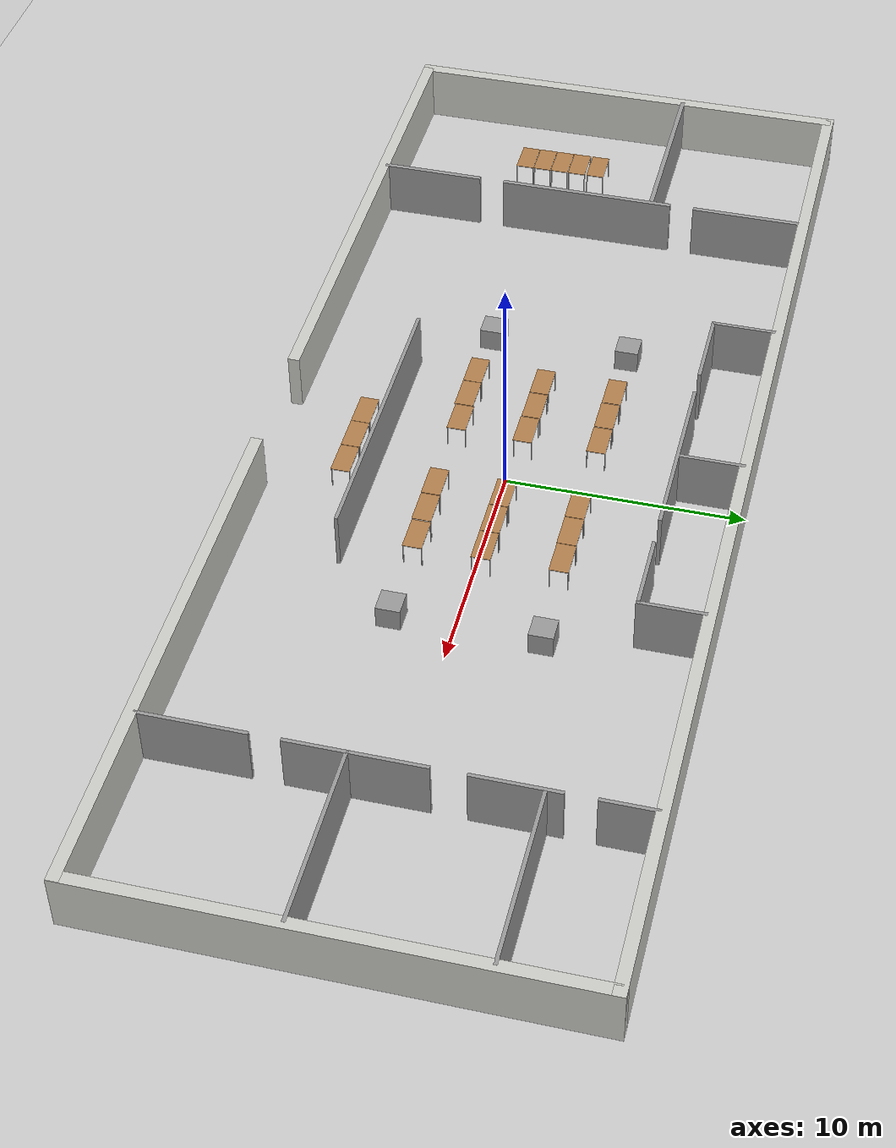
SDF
<sdf version="1.6">
 <world name="default">
  <light name="sun" type="directional">
   <pose>0 0 10 0 -0 0</pose>
   <diffuse>0.8 0.8 0.8 1</diffuse>
   <specular>0.2 0.2 0.2 1</specular>
   <attenuation>
    <range>1000</range>
    <constant>0.9</constant>
    <linear>0.01</linear>
    <quadratic>0.001</quadratic>
   </attenuation>
   <direction>-0.5 0.1 -0.9</direction>
  </light>
  <model name="ground_plane">
   <static>1</static>
   <link name="link">
    <collision name="collision">
     <geometry><plane><normal>0 0 1</normal><size>100 100</size></plane></geometry>
     <surface><friction><ode><mu>100</mu><mu2>50</mu2></ode></friction></surface>
    </collision>
    <visual name="visual">
     <cast_shadows>0</cast_shadows>
     <geometry><plane><normal>0 0 1</normal><size>100 100</size></plane></geometry>
     <material>
      <script><uri>file://media/materials/scripts/gazebo.material</uri><name>Gazebo/Grey</name></script>
     </material>
    </visual>
   </link>
  </model>
  <gravity>0 0 -9.8</gravity>
  <magnetic_field>6e-06 2.3e-05 -4.2e-05</magnetic_field>
  <atmosphere type="adiabatic"/>
  <physics name="default_physics" default="0" type="ode">
   <max_step_size>0.001</max_step_size>
   <real_time_factor>1</real_time_factor>
   <real_time_update_rate>1000</real_time_update_rate>
  </physics>
  <scene><ambient>0.4 0.4 0.4 1</ambient><background>0.7 0.7 0.7 1</background><shadows>1</shadows></scene>
  <audio><device>default</device></audio>
  <spherical_coordinates>
   <surface_model>EARTH_WGS84</surface_model>
   <latitude_deg>0</latitude_deg>
   <longitude_deg>0</longitude_deg>
   <elevation>0</elevation>
   <heading_deg>0</heading_deg>
  </spherical_coordinates>
  <model name="indemind_office">
   <pose>-0.031352 0.007006 0 0 -0 0</pose>
   <link name="Wall_1">
    <collision name="Wall_1_Collision">
     <geometry><box><size>20 0.5 2.5</size></box></geometry>
     <pose>0 0 1.25 0 -0 0</pose>
    </collision>
    <visual name="Wall_1_Visual">
     <pose>0 0 1.25 0 -0 0</pose>
     <geometry><box><size>20 0.5 2.5</size></box></geometry>
     <material>
      <script><uri>file://media/materials/scripts/gazebo.material</uri><name>Gazebo/CeilingTiled</name></script>
      <ambient>1 1 1 1</ambient>
     </material>
     <meta><layer>0</layer></meta>
    </visual>
    <pose>-24.75 -0 0 0 -0 -1.5708</pose>
   </link>
   <link name="Wall_11">
    <collision name="Wall_11_Collision">
     <geometry><box><size>20 0.5 2.5</size></box></geometry>
     <pose>0 0 1.25 0 -0 0</pose>
    </collision>
    <visual name="Wall_11_Visual">
     <pose>0 0 1.25 0 -0 0</pose>
     <geometry><box><size>20 0.5 2.5</size></box></geometry>
     <material>
      <script><uri>file://media/materials/scripts/gazebo.material</uri><name>Gazebo/CeilingTiled</name></script>
      <ambient>1 1 1 1</ambient>
     </material>
     <meta><layer>0</layer></meta>
    </visual>
    <pose>24.75 -0 0 0 -0 -1.5708</pose>
   </link>
   <link name="Wall_13">
    <collision name="Wall_13_Collision">
     <geometry><box><size>4.80017 0.2 2.5</size></box></geometry>
     <pose>0 0 1.25 0 -0 0</pose>
    </collision>
    <visual name="Wall_13_Visual">
     <pose>0 0 1.25 0 -0 0</pose>
     <geometry><box><size>4.80017 0.2 2.5</size></box></geometry>
     <material>
      <script><uri>file://media/materials/scripts/gazebo.material</uri><name>Gazebo/Grey</name></script>
      <ambient>1 1 1 1</ambient>
     </material>
     <meta><layer>0</layer></meta>
    </visual>
    <pose>-16.658 7.127 0 0 -0 -1.5708</pose>
   </link>
   <link name="Wall_15">
    <collision name="Wall_15_Collision">
     <geometry><box><size>7.75 0.2 2.5</size></box></geometry>
     <pose>0 0 1.25 0 -0 0</pose>
    </collision>
    <visual name="Wall_15_Visual">
     <pose>0 0 1.25 0 -0 0</pose>
     <geometry><box><size>7.75 0.2 2.5</size></box></geometry>
     <material>
      <script><uri>file://media/materials/scripts/gazebo.material</uri><name>Gazebo/Grey</name></script>
      <ambient>1 1 1 1</ambient>
     </material>
     <meta><layer>0</layer></meta>
    </visual>
    <pose>-16.658 -0.198 0 0 -0 -1.5708</pose>
   </link>
   <link name="Wall_17">
    <collision name="Wall_17_Collision">
     <geometry><box><size>4.5 0.2 2.5</size></box></geometry>
     <pose>0 0 1.25 0 -0 0</pose>
    </collision>
    <visual name="Wall_17_Visual">
     <pose>0 0 1.25 0 -0 0</pose>
     <geometry><box><size>4.5 0.2 2.5</size></box></geometry>
     <material>
      <script><uri>file://media/materials/scripts/gazebo.material</uri><name>Gazebo/Grey</name></script>
      <ambient>1 1 1 1</ambient>
     </material>
     <meta><layer>0</layer></meta>
    </visual>
    <pose>-16.658 -7.423 0 0 -0 -1.5708</pose>
   </link>
   <link name="Wall_19">
    <collision name="Wall_19_Collision">
     <geometry><box><size>8.04985 0.2 2.5</size></box></geometry>
     <pose>0 0 1.25 0 -0 0</pose>
    </collision>
    <visual name="Wall_19_Visual">
     <pose>0 0 1.25 0 -0 0</pose>
     <geometry><box><size>8.04985 0.2 2.5</size></box></geometry>
     <material>
      <script><uri>file://media/materials/scripts/gazebo.material</uri><name>Gazebo/Grey</name></script>
      <ambient>1 1 1 1</ambient>
     </material>
     <meta><layer>0</layer></meta>
    </visual>
    <pose>-20.703 2.792 0 0 -0 0</pose>
   </link>
   <link name="Wall_21">
    <collision name="Wall_21_Collision">
     <geometry><box><size>2.25 0.15 2.5</size></box></geometry>
     <pose>0 0 1.25 0 -0 0</pose>
    </collision>
    <visual name="Wall_21_Visual">
     <pose>0 0 1.25 0 -0 0</pose>
     <geometry><box><size>2.25 0.15 2.5</size></box></geometry>
     <material>
      <script><uri>file://media/materials/scripts/gazebo.material</uri><name>Gazebo/Grey</name></script>
      <ambient>1 1 1 1</ambient>
     </material>
     <meta><layer>0</layer></meta>
    </visual>
    <pose>17.2839 8.57905 0 0 -0 -1.57072</pose>
   </link>
   <link name="Wall_23">
    <collision name="Wall_23_Collision">
     <geometry><box><size>3.5 0.15 2.5</size></box></geometry>
     <pose>0 0 1.25 0 -0 0</pose>
    </collision>
    <visual name="Wall_23_Visual">
     <pose>0 0 1.25 0 -0 0</pose>
     <geometry><box><size>3.5 0.15 2.5</size></box></geometry>
     <material>
      <script><uri>file://media/materials/scripts/gazebo.material</uri><name>Gazebo/Grey</name></script>
      <ambient>1 1 1 1</ambient>
     </material>
     <meta><layer>0</layer></meta>
    </visual>
    <pose>17.2838 4.5041 0 0 -0 -1.5708</pose>
   </link>
   <link name="Wall_25">
    <collision name="Wall_25_Collision">
     <geometry><box><size>5.5 0.15 2.5</size></box></geometry>
     <pose>0 0 1.25 0 -0 0</pose>
    </collision>
    <visual name="Wall_25_Visual">
     <pose>0 0 1.25 0 -0 0</pose>
     <geometry><box><size>5.5 0.15 2.5</size></box></geometry>
     <material>
      <script><uri>file://media/materials/scripts/gazebo.material</uri><name>Gazebo/Grey</name></script>
      <ambient>1 1 1 1</ambient>
     </material>
     <meta><layer>0</layer></meta>
    </visual>
    <pose>17.2838 -1.3459 0 0 -0 -1.5708</pose>
   </link>
   <link name="Wall_27">
    <collision name="Wall_27_Collision">
     <geometry><box><size>4.35 0.15 2.5</size></box></geometry>
     <pose>0 0 1.25 0 -0 0</pose>
    </collision>
    <visual name="Wall_27_Visual">
     <pose>0 0 1.25 0 -0 0</pose>
     <geometry><box><size>4.35 0.15 2.5</size></box></geometry>
     <material>
      <script><uri>file://media/materials/scripts/gazebo.material</uri><name>Gazebo/Grey</name></script>
      <ambient>1 1 1 1</ambient>
     </material>
     <meta><layer>0</layer></meta>
    </visual>
    <pose>17.2838 -7.4709 0 0 -0 -1.5708</pose>
   </link>
   <link name="Wall_29">
    <collision name="Wall_29_Collision">
     <geometry><box><size>7.5 0.15 2.5</size></box></geometry>
     <pose>0 0 1.25 0 -0 0</pose>
    </collision>
    <visual name="Wall_29_Visual">
     <pose>0 0 1.25 0 -0 0</pose>
     <geometry><box><size>7.5 0.15 2.5</size></box></geometry>
     <material>
      <script><uri>file://media/materials/scripts/gazebo.material</uri><name>Gazebo/Grey</name></script>
      <ambient>1 1 1 1</ambient>
     </material>
     <meta><layer>0</layer></meta>
    </visual>
    <pose>20.9993 5.58355 0 0 -0 0</pose>
   </link>
   <link name="Wall_3">
    <collision name="Wall_3_Collision">
     <geometry><box><size>50 0.5 2.5</size></box></geometry>
     <pose>0 0 1.25 0 -0 0</pose>
    </collision>
    <visual name="Wall_3_Visual">
     <pose>0 0 1.25 0 -0 0</pose>
     <geometry><box><size>50 0.5 2.5</size></box></geometry>
     <material>
      <script><uri>file://media/materials/scripts/gazebo.material</uri><name>Gazebo/CeilingTiled</name></script>
      <ambient>1 1 1 1</ambient>
     </material>
     <meta><layer>0</layer></meta>
    </visual>
    <pose>-1e-06 9.75 0 0 -0 0</pose>
   </link>
   <link name="Wall_31">
    <collision name="Wall_31_Collision">
     <geometry><box><size>7.5 0.15 2.5</size></box></geometry>
     <pose>0 0 1.25 0 -0 0</pose>
    </collision>
    <visual name="Wall_31_Visual">
     <pose>0 0 1.25 0 -0 0</pose>
     <geometry><box><size>7.5 0.15 2.5</size></box></geometry>
     <material>
      <script><uri>file://media/materials/scripts/gazebo.material</uri><name>Gazebo/Grey</name></script>
      <ambient>1 1 1 1</ambient>
     </material>
     <meta><layer>0</layer></meta>
    </visual>
    <pose>20.9993 -1.658 0 0 -0 0</pose>
   </link>
   <link name="Wall_34">
    <collision name="Wall_34_Collision">
     <geometry><box><size>2.75032 0.15 2.5</size></box></geometry>
     <pose>0 0 1.25 0 -0 0</pose>
    </collision>
    <visual name="Wall_34_Visual">
     <pose>0 0 1.25 0 -0 0</pose>
     <geometry><box><size>2.75032 0.15 2.5</size></box></geometry>
     <material>
      <script><uri>file://media/materials/scripts/gazebo.material</uri><name>Gazebo/Grey</name></script>
      <ambient>1 1 1 1</ambient>
     </material>
     <meta><layer>0</layer></meta>
    </visual>
    <pose>-8.97184 8.28865 0 0 -0 -1.5708</pose>
   </link>
   <link name="Wall_35">
    <collision name="Wall_35_Collision">
     <geometry><box><size>3.5 0.15 2.5</size></box></geometry>
     <pose>0 0 1.25 0 -0 0</pose>
    </collision>
    <visual name="Wall_35_Visual">
     <pose>0 0 1.25 0 -0 0</pose>
     <geometry><box><size>3.5 0.15 2.5</size></box></geometry>
     <material>
      <script><uri>file://media/materials/scripts/gazebo.material</uri><name>Gazebo/Grey</name></script>
      <ambient>1 1 1 1</ambient>
     </material>
     <meta><layer>0</layer></meta>
    </visual>
    <pose>-7.25638 6.98865 0 0 -0 0</pose>
   </link>
   <link name="Wall_37">
    <collision name="Wall_37_Collision">
     <geometry><box><size>7.75 0.15 2.5</size></box></geometry>
     <pose>0 0 1.25 0 -0 0</pose>
    </collision>
    <visual name="Wall_37_Visual">
     <pose>0 0 1.25 0 -0 0</pose>
     <geometry><box><size>7.75 0.15 2.5</size></box></geometry>
     <material>
      <script><uri>file://media/materials/scripts/gazebo.material</uri><name>Gazebo/Grey</name></script>
      <ambient>1 1 1 1</ambient>
     </material>
     <meta><layer>0</layer></meta>
    </visual>
    <pose>-0.572001 6.989 0 0 -0 0</pose>
   </link>
   <link name="Wall_39">
    <collision name="Wall_39_Collision">
     <geometry><box><size>3.35 0.15 2.5</size></box></geometry>
     <pose>0 0 1.25 0 -0 0</pose>
    </collision>
    <visual name="Wall_39_Visual">
     <pose>0 0 1.25 0 -0 0</pose>
     <geometry><box><size>3.35 0.15 2.5</size></box></geometry>
     <material>
      <script><uri>file://media/materials/scripts/gazebo.material</uri><name>Gazebo/Grey</name></script>
      <ambient>1 1 1 1</ambient>
     </material>
     <meta><layer>0</layer></meta>
    </visual>
    <pose>6.17808 6.98882 0 0 -0 -0.00011</pose>
   </link>
   <link name="Wall_40">
    <collision name="Wall_40_Collision">
     <geometry><box><size>2.75 0.15 2.5</size></box></geometry>
     <pose>0 0 1.25 0 -0 0</pose>
    </collision>
    <visual name="Wall_40_Visual">
     <pose>0 0 1.25 0 -0 0</pose>
     <geometry><box><size>2.75 0.15 2.5</size></box></geometry>
     <material>
      <script><uri>file://media/materials/scripts/gazebo.material</uri><name>Gazebo/Grey</name></script>
      <ambient>1 1 1 1</ambient>
     </material>
     <meta><layer>0</layer></meta>
    </visual>
    <pose>7.77816 8.28865 0 0 -0 1.5708</pose>
   </link>
   <link name="Wall_42">
    <collision name="Wall_42_Collision">
     <geometry><box><size>2.75 0.15 2.5</size></box></geometry>
     <pose>0 0 1.25 0 -0 0</pose>
    </collision>
    <visual name="Wall_42_Visual">
     <pose>0 0 1.25 0 -0 0</pose>
     <geometry><box><size>2.75 0.15 2.5</size></box></geometry>
     <material>
      <script><uri>file://media/materials/scripts/gazebo.material</uri><name>Gazebo/Grey</name></script>
      <ambient>1 1 1 1</ambient>
     </material>
     <meta><layer>0</layer></meta>
    </visual>
    <pose>-0.516625 8.36956 0 0 -0 -1.5708</pose>
   </link>
   <link name="Wall_44">
    <collision name="Wall_44_Collision">
     <geometry><box><size>12.5 0.15 2.5</size></box></geometry>
     <pose>0 0 1.25 0 -0 0</pose>
    </collision>
    <visual name="Wall_44_Visual">
     <pose>0 0 1.25 0 -0 0</pose>
     <geometry><box><size>12.5 0.15 2.5</size></box></geometry>
     <material>
      <script><uri>file://media/materials/scripts/gazebo.material</uri><name>Gazebo/Grey</name></script>
      <ambient>1 1 1 1</ambient>
     </material>
     <meta><layer>0</layer></meta>
    </visual>
    <pose>-0.086317 -5.33946 0 0 -0 0</pose>
   </link>
   <link name="Wall_7">
    <collision name="Wall_7_Collision">
     <geometry><box><size>22.5 0.5 2.5</size></box></geometry>
     <pose>0 0 1.25 0 -0 0</pose>
    </collision>
    <visual name="Wall_7_Visual">
     <pose>0 0 1.25 0 -0 0</pose>
     <geometry><box><size>22.5 0.5 2.5</size></box></geometry>
     <material>
      <script><uri>file://media/materials/scripts/gazebo.material</uri><name>Gazebo/CeilingTiled</name></script>
      <ambient>1 1 1 1</ambient>
     </material>
     <meta><layer>0</layer></meta>
    </visual>
    <pose>-13.75 -9.75 0 0 -0 0</pose>
   </link>
   <link name="Wall_9">
    <collision name="Wall_9_Collision">
     <geometry><box><size>22.5 0.5 2.5</size></box></geometry>
     <pose>0 0 1.25 0 -0 0</pose>
    </collision>
    <visual name="Wall_9_Visual">
     <pose>0 0 1.25 0 -0 0</pose>
     <geometry><box><size>22.5 0.5 2.5</size></box></geometry>
     <material>
      <script><uri>file://media/materials/scripts/gazebo.material</uri><name>Gazebo/CeilingTiled</name></script>
      <ambient>1 1 1 1</ambient>
     </material>
     <meta><layer>0</layer></meta>
    </visual>
    <pose>13.7296 -9.74954 0 0 -0 0</pose>
   </link>
   <static>1</static>
  </model>
  <model name="table">
   <static>1</static>
   <link name="link">
    <collision name="surface">
     <pose>0 0 1 0 -0 0</pose>
     <geometry><box><size>1.5 0.8 0.03</size></box></geometry>
     <surface><friction><ode><mu>0.6</mu><mu2>0.6</mu2></ode></friction></surface>
    </collision>
    <visual name="visual1">
     <pose>0 0 1 0 -0 0</pose>
     <geometry><box><size>1.5 0.8 0.03</size></box></geometry>
     <material>
      <script><uri>file://media/materials/scripts/gazebo.material</uri><name>Gazebo/Wood</name></script>
     </material>
    </visual>
    <collision name="front_left_leg">
     <pose>0.68 0.38 0.5 0 -0 0</pose>
     <geometry><cylinder><radius>0.02</radius><length>1</length></cylinder></geometry>
    </collision>
    <visual name="front_left_leg">
     <pose>0.68 0.38 0.5 0 -0 0</pose>
     <geometry><cylinder><radius>0.02</radius><length>1</length></cylinder></geometry>
     <material>
      <script><uri>file://media/materials/scripts/gazebo.material</uri><name>Gazebo/Grey</name></script>
     </material>
    </visual>
    <collision name="front_right_leg">
     <pose>0.68 -0.38 0.5 0 -0 0</pose>
     <geometry><cylinder><radius>0.02</radius><length>1</length></cylinder></geometry>
    </collision>
    <visual name="front_right_leg">
     <pose>0.68 -0.38 0.5 0 -0 0</pose>
     <geometry><cylinder><radius>0.02</radius><length>1</length></cylinder></geometry>
     <material>
      <script><uri>file://media/materials/scripts/gazebo.material</uri><name>Gazebo/Grey</name></script>
     </material>
    </visual>
    <collision name="back_right_leg">
     <pose>-0.68 -0.38 0.5 0 -0 0</pose>
     <geometry><cylinder><radius>0.02</radius><length>1</length></cylinder></geometry>
    </collision>
    <visual name="back_right_leg">
     <pose>-0.68 -0.38 0.5 0 -0 0</pose>
     <geometry><cylinder><radius>0.02</radius><length>1</length></cylinder></geometry>
     <material>
      <script><uri>file://media/materials/scripts/gazebo.material</uri><name>Gazebo/Grey</name></script>
     </material>
    </visual>
    <collision name="back_left_leg">
     <pose>-0.68 0.38 0.5 0 -0 0</pose>
     <geometry><cylinder><radius>0.02</radius><length>1</length></cylinder></geometry>
    </collision>
    <visual name="back_left_leg">
     <pose>-0.68 0.38 0.5 0 -0 0</pose>
     <geometry><cylinder><radius>0.02</radius><length>1</length></cylinder></geometry>
     <material>
      <script><uri>file://media/materials/scripts/gazebo.material</uri><name>Gazebo/Grey</name></script>
     </material>
    </visual>
   </link>
   <pose>-1.77581 -6.45658 0 0 -0 0</pose>
  </model>
  <model name="table_0">
   <static>1</static>
   <link name="link">
    <collision name="surface">
     <pose>0 0 1 0 -0 0</pose>
     <geometry><box><size>1.5 0.8 0.03</size></box></geometry>
     <surface><friction><ode><mu>0.6</mu><mu2>0.6</mu2></ode></friction></surface>
    </collision>
    <visual name="visual1">
     <pose>0 0 1 0 -0 0</pose>
     <geometry><box><size>1.5 0.8 0.03</size></box></geometry>
     <material>
      <script><uri>file://media/materials/scripts/gazebo.material</uri><name>Gazebo/Wood</name></script>
     </material>
    </visual>
    <collision name="front_left_leg">
     <pose>0.68 0.38 0.5 0 -0 0</pose>
     <geometry><cylinder><radius>0.02</radius><length>1</length></cylinder></geometry>
    </collision>
    <visual name="front_left_leg">
     <pose>0.68 0.38 0.5 0 -0 0</pose>
     <geometry><cylinder><radius>0.02</radius><length>1</length></cylinder></geometry>
     <material>
      <script><uri>file://media/materials/scripts/gazebo.material</uri><name>Gazebo/Grey</name></script>
     </material>
    </visual>
    <collision name="front_right_leg">
     <pose>0.68 -0.38 0.5 0 -0 0</pose>
     <geometry><cylinder><radius>0.02</radius><length>1</length></cylinder></geometry>
    </collision>
    <visual name="front_right_leg">
     <pose>0.68 -0.38 0.5 0 -0 0</pose>
     <geometry><cylinder><radius>0.02</radius><length>1</length></cylinder></geometry>
     <material>
      <script><uri>file://media/materials/scripts/gazebo.material</uri><name>Gazebo/Grey</name></script>
     </material>
    </visual>
    <collision name="back_right_leg">
     <pose>-0.68 -0.38 0.5 0 -0 0</pose>
     <geometry><cylinder><radius>0.02</radius><length>1</length></cylinder></geometry>
    </collision>
    <visual name="back_right_leg">
     <pose>-0.68 -0.38 0.5 0 -0 0</pose>
     <geometry><cylinder><radius>0.02</radius><length>1</length></cylinder></geometry>
     <material>
      <script><uri>file://media/materials/scripts/gazebo.material</uri><name>Gazebo/Grey</name></script>
     </material>
    </visual>
    <collision name="back_left_leg">
     <pose>-0.68 0.38 0.5 0 -0 0</pose>
     <geometry><cylinder><radius>0.02</radius><length>1</length></cylinder></geometry>
    </collision>
    <visual name="back_left_leg">
     <pose>-0.68 0.38 0.5 0 -0 0</pose>
     <geometry><cylinder><radius>0.02</radius><length>1</length></cylinder></geometry>
     <material>
      <script><uri>file://media/materials/scripts/gazebo.material</uri><name>Gazebo/Grey</name></script>
     </material>
    </visual>
   </link>
   <pose>-0.266949 -6.45533 0 0 -0 0</pose>
  </model>
  <model name="table_1">
   <static>1</static>
   <link name="link">
    <collision name="surface">
     <pose>0 0 1 0 -0 0</pose>
     <geometry><box><size>1.5 0.8 0.03</size></box></geometry>
     <surface><friction><ode><mu>0.6</mu><mu2>0.6</mu2></ode></friction></surface>
    </collision>
    <visual name="visual1">
     <pose>0 0 1 0 -0 0</pose>
     <geometry><box><size>1.5 0.8 0.03</size></box></geometry>
     <material>
      <script><uri>file://media/materials/scripts/gazebo.material</uri><name>Gazebo/Wood</name></script>
     </material>
    </visual>
    <collision name="front_left_leg">
     <pose>0.68 0.38 0.5 0 -0 0</pose>
     <geometry><cylinder><radius>0.02</radius><length>1</length></cylinder></geometry>
    </collision>
    <visual name="front_left_leg">
     <pose>0.68 0.38 0.5 0 -0 0</pose>
     <geometry><cylinder><radius>0.02</radius><length>1</length></cylinder></geometry>
     <material>
      <script><uri>file://media/materials/scripts/gazebo.material</uri><name>Gazebo/Grey</name></script>
     </material>
    </visual>
    <collision name="front_right_leg">
     <pose>0.68 -0.38 0.5 0 -0 0</pose>
     <geometry><cylinder><radius>0.02</radius><length>1</length></cylinder></geometry>
    </collision>
    <visual name="front_right_leg">
     <pose>0.68 -0.38 0.5 0 -0 0</pose>
     <geometry><cylinder><radius>0.02</radius><length>1</length></cylinder></geometry>
     <material>
      <script><uri>file://media/materials/scripts/gazebo.material</uri><name>Gazebo/Grey</name></script>
     </material>
    </visual>
    <collision name="back_right_leg">
     <pose>-0.68 -0.38 0.5 0 -0 0</pose>
     <geometry><cylinder><radius>0.02</radius><length>1</length></cylinder></geometry>
    </collision>
    <visual name="back_right_leg">
     <pose>-0.68 -0.38 0.5 0 -0 0</pose>
     <geometry><cylinder><radius>0.02</radius><length>1</length></cylinder></geometry>
     <material>
      <script><uri>file://media/materials/scripts/gazebo.material</uri><name>Gazebo/Grey</name></script>
     </material>
    </visual>
    <collision name="back_left_leg">
     <pose>-0.68 0.38 0.5 0 -0 0</pose>
     <geometry><cylinder><radius>0.02</radius><length>1</length></cylinder></geometry>
    </collision>
    <visual name="back_left_leg">
     <pose>-0.68 0.38 0.5 0 -0 0</pose>
     <geometry><cylinder><radius>0.02</radius><length>1</length></cylinder></geometry>
     <material>
      <script><uri>file://media/materials/scripts/gazebo.material</uri><name>Gazebo/Grey</name></script>
     </material>
    </visual>
   </link>
   <pose>1.24514 -6.45321 0 0 -0 0</pose>
  </model>
  <model name="unit_box">
   <pose>-8.43298 3.46662 0.499995 -1e-05 -0 -0</pose>
   <link name="link">
    <inertial>
     <mass>1</mass>
     <inertia>
      <ixx>0.166667</ixx>
      <ixy>0</ixy>
      <ixz>0</ixz>
      <iyy>0.166667</iyy>
      <iyz>0</iyz>
      <izz>0.166667</izz>
     </inertia>
    </inertial>
    <collision name="collision"><geometry><box><size>1 1 1</size></box></geometry></collision>
    <visual name="visual">
     <geometry><box><size>1 1 1</size></box></geometry>
     <material>
      <script><name>Gazebo/Grey</name><uri>file://media/materials/scripts/gazebo.material</uri></script>
     </material>
    </visual>
   </link>
  </model>
  <model name="unit_box_0">
   <pose>-8.43126 -2.51767 0.499995 0 1e-05 0</pose>
   <link name="link">
    <inertial>
     <mass>1</mass>
     <inertia>
      <ixx>0.166667</ixx>
      <ixy>0</ixy>
      <ixz>0</ixz>
      <iyy>0.166667</iyy>
      <iyz>0</iyz>
      <izz>0.166667</izz>
     </inertia>
    </inertial>
    <collision name="collision"><geometry><box><size>1 1 1</size></box></geometry></collision>
    <visual name="visual">
     <geometry><box><size>1 1 1</size></box></geometry>
     <material>
      <script><name>Gazebo/Grey</name><uri>file://media/materials/scripts/gazebo.material</uri></script>
     </material>
    </visual>
   </link>
  </model>
  <model name="unit_box_1">
   <pose>8.49375 3.54195 0.499995 -1e-05 -0 0</pose>
   <link name="link">
    <inertial>
     <mass>1</mass>
     <inertia>
      <ixx>0.166667</ixx>
      <ixy>0</ixy>
      <ixz>0</ixz>
      <iyy>0.166667</iyy>
      <iyz>0</iyz>
      <izz>0.166667</izz>
     </inertia>
    </inertial>
    <collision name="collision"><geometry><box><size>1 1 1</size></box></geometry></collision>
    <visual name="visual">
     <geometry><box><size>1 1 1</size></box></geometry>
     <material>
      <script><name>Gazebo/Grey</name><uri>file://media/materials/scripts/gazebo.material</uri></script>
     </material>
    </visual>
   </link>
  </model>
  <model name="unit_box_2">
   <pose>8.52634 -2.49408 0.5 0 -0 0</pose>
   <link name="link">
    <inertial>
     <mass>1</mass>
     <inertia>
      <ixx>0.166667</ixx>
      <ixy>0</ixy>
      <ixz>0</ixz>
      <iyy>0.166667</iyy>
      <iyz>0</iyz>
      <izz>0.166667</izz>
     </inertia>
    </inertial>
    <collision name="collision"><geometry><box><size>1 1 1</size></box></geometry></collision>
    <visual name="visual">
     <geometry><box><size>1 1 1</size></box></geometry>
     <material>
      <script><name>Gazebo/Grey</name><uri>file://media/materials/scripts/gazebo.material</uri></script>
     </material>
    </visual>
   </link>
  </model>
  <model name="table_2">
   <static>1</static>
   <link name="link">
    <collision name="surface">
     <pose>0 0 1 0 -0 0</pose>
     <geometry><box><size>1.5 0.8 0.03</size></box></geometry>
     <surface><friction><ode><mu>0.6</mu><mu2>0.6</mu2></ode></friction></surface>
    </collision>
    <visual name="visual1">
     <pose>0 0 1 0 -0 0</pose>
     <geometry><box><size>1.5 0.8 0.03</size></box></geometry>
     <material>
      <script><uri>file://media/materials/scripts/gazebo.material</uri><name>Gazebo/Wood</name></script>
     </material>
    </visual>
    <collision name="front_left_leg">
     <pose>0.68 0.38 0.5 0 -0 0</pose>
     <geometry><cylinder><radius>0.02</radius><length>1</length></cylinder></geometry>
    </collision>
    <visual name="front_left_leg">
     <pose>0.68 0.38 0.5 0 -0 0</pose>
     <geometry><cylinder><radius>0.02</radius><length>1</length></cylinder></geometry>
     <material>
      <script><uri>file://media/materials/scripts/gazebo.material</uri><name>Gazebo/Grey</name></script>
     </material>
    </visual>
    <collision name="front_right_leg">
     <pose>0.68 -0.38 0.5 0 -0 0</pose>
     <geometry><cylinder><radius>0.02</radius><length>1</length></cylinder></geometry>
    </collision>
    <visual name="front_right_leg">
     <pose>0.68 -0.38 0.5 0 -0 0</pose>
     <geometry><cylinder><radius>0.02</radius><length>1</length></cylinder></geometry>
     <material>
      <script><uri>file://media/materials/scripts/gazebo.material</uri><name>Gazebo/Grey</name></script>
     </material>
    </visual>
    <collision name="back_right_leg">
     <pose>-0.68 -0.38 0.5 0 -0 0</pose>
     <geometry><cylinder><radius>0.02</radius><length>1</length></cylinder></geometry>
    </collision>
    <visual name="back_right_leg">
     <pose>-0.68 -0.38 0.5 0 -0 0</pose>
     <geometry><cylinder><radius>0.02</radius><length>1</length></cylinder></geometry>
     <material>
      <script><uri>file://media/materials/scripts/gazebo.material</uri><name>Gazebo/Grey</name></script>
     </material>
    </visual>
    <collision name="back_left_leg">
     <pose>-0.68 0.38 0.5 0 -0 0</pose>
     <geometry><cylinder><radius>0.02</radius><length>1</length></cylinder></geometry>
    </collision>
    <visual name="back_left_leg">
     <pose>-0.68 0.38 0.5 0 -0 0</pose>
     <geometry><cylinder><radius>0.02</radius><length>1</length></cylinder></geometry>
     <material>
      <script><uri>file://media/materials/scripts/gazebo.material</uri><name>Gazebo/Grey</name></script>
     </material>
    </visual>
   </link>
   <pose>-5.31157 3.49328 0 0 -0 0</pose>
  </model>
  <model name="table_3">
   <static>1</static>
   <link name="link">
    <collision name="surface">
     <pose>0 0 1 0 -0 0</pose>
     <geometry><box><size>1.5 0.8 0.03</size></box></geometry>
     <surface><friction><ode><mu>0.6</mu><mu2>0.6</mu2></ode></friction></surface>
    </collision>
    <visual name="visual1">
     <pose>0 0 1 0 -0 0</pose>
     <geometry><box><size>1.5 0.8 0.03</size></box></geometry>
     <material>
      <script><uri>file://media/materials/scripts/gazebo.material</uri><name>Gazebo/Wood</name></script>
     </material>
    </visual>
    <collision name="front_left_leg">
     <pose>0.68 0.38 0.5 0 -0 0</pose>
     <geometry><cylinder><radius>0.02</radius><length>1</length></cylinder></geometry>
    </collision>
    <visual name="front_left_leg">
     <pose>0.68 0.38 0.5 0 -0 0</pose>
     <geometry><cylinder><radius>0.02</radius><length>1</length></cylinder></geometry>
     <material>
      <script><uri>file://media/materials/scripts/gazebo.material</uri><name>Gazebo/Grey</name></script>
     </material>
    </visual>
    <collision name="front_right_leg">
     <pose>0.68 -0.38 0.5 0 -0 0</pose>
     <geometry><cylinder><radius>0.02</radius><length>1</length></cylinder></geometry>
    </collision>
    <visual name="front_right_leg">
     <pose>0.68 -0.38 0.5 0 -0 0</pose>
     <geometry><cylinder><radius>0.02</radius><length>1</length></cylinder></geometry>
     <material>
      <script><uri>file://media/materials/scripts/gazebo.material</uri><name>Gazebo/Grey</name></script>
     </material>
    </visual>
    <collision name="back_right_leg">
     <pose>-0.68 -0.38 0.5 0 -0 0</pose>
     <geometry><cylinder><radius>0.02</radius><length>1</length></cylinder></geometry>
    </collision>
    <visual name="back_right_leg">
     <pose>-0.68 -0.38 0.5 0 -0 0</pose>
     <geometry><cylinder><radius>0.02</radius><length>1</length></cylinder></geometry>
     <material>
      <script><uri>file://media/materials/scripts/gazebo.material</uri><name>Gazebo/Grey</name></script>
     </material>
    </visual>
    <collision name="back_left_leg">
     <pose>-0.68 0.38 0.5 0 -0 0</pose>
     <geometry><cylinder><radius>0.02</radius><length>1</length></cylinder></geometry>
    </collision>
    <visual name="back_left_leg">
     <pose>-0.68 0.38 0.5 0 -0 0</pose>
     <geometry><cylinder><radius>0.02</radius><length>1</length></cylinder></geometry>
     <material>
      <script><uri>file://media/materials/scripts/gazebo.material</uri><name>Gazebo/Grey</name></script>
     </material>
    </visual>
   </link>
   <pose>-3.76952 3.48462 0 0 -0 0</pose>
  </model>
  <model name="table_4">
   <static>1</static>
   <link name="link">
    <collision name="surface">
     <pose>0 0 1 0 -0 0</pose>
     <geometry><box><size>1.5 0.8 0.03</size></box></geometry>
     <surface><friction><ode><mu>0.6</mu><mu2>0.6</mu2></ode></friction></surface>
    </collision>
    <visual name="visual1">
     <pose>0 0 1 0 -0 0</pose>
     <geometry><box><size>1.5 0.8 0.03</size></box></geometry>
     <material>
      <script><uri>file://media/materials/scripts/gazebo.material</uri><name>Gazebo/Wood</name></script>
     </material>
    </visual>
    <collision name="front_left_leg">
     <pose>0.68 0.38 0.5 0 -0 0</pose>
     <geometry><cylinder><radius>0.02</radius><length>1</length></cylinder></geometry>
    </collision>
    <visual name="front_left_leg">
     <pose>0.68 0.38 0.5 0 -0 0</pose>
     <geometry><cylinder><radius>0.02</radius><length>1</length></cylinder></geometry>
     <material>
      <script><uri>file://media/materials/scripts/gazebo.material</uri><name>Gazebo/Grey</name></script>
     </material>
    </visual>
    <collision name="front_right_leg">
     <pose>0.68 -0.38 0.5 0 -0 0</pose>
     <geometry><cylinder><radius>0.02</radius><length>1</length></cylinder></geometry>
    </collision>
    <visual name="front_right_leg">
     <pose>0.68 -0.38 0.5 0 -0 0</pose>
     <geometry><cylinder><radius>0.02</radius><length>1</length></cylinder></geometry>
     <material>
      <script><uri>file://media/materials/scripts/gazebo.material</uri><name>Gazebo/Grey</name></script>
     </material>
    </visual>
    <collision name="back_right_leg">
     <pose>-0.68 -0.38 0.5 0 -0 0</pose>
     <geometry><cylinder><radius>0.02</radius><length>1</length></cylinder></geometry>
    </collision>
    <visual name="back_right_leg">
     <pose>-0.68 -0.38 0.5 0 -0 0</pose>
     <geometry><cylinder><radius>0.02</radius><length>1</length></cylinder></geometry>
     <material>
      <script><uri>file://media/materials/scripts/gazebo.material</uri><name>Gazebo/Grey</name></script>
     </material>
    </visual>
    <collision name="back_left_leg">
     <pose>-0.68 0.38 0.5 0 -0 0</pose>
     <geometry><cylinder><radius>0.02</radius><length>1</length></cylinder></geometry>
    </collision>
    <visual name="back_left_leg">
     <pose>-0.68 0.38 0.5 0 -0 0</pose>
     <geometry><cylinder><radius>0.02</radius><length>1</length></cylinder></geometry>
     <material>
      <script><uri>file://media/materials/scripts/gazebo.material</uri><name>Gazebo/Grey</name></script>
     </material>
    </visual>
   </link>
   <pose>-2.2286 3.48108 0 0 -0 0</pose>
  </model>
  <model name="table_6">
   <static>1</static>
   <link name="link">
    <collision name="surface">
     <pose>0 0 1 0 -0 0</pose>
     <geometry><box><size>1.5 0.8 0.03</size></box></geometry>
     <surface><friction><ode><mu>0.6</mu><mu2>0.6</mu2></ode></friction></surface>
    </collision>
    <visual name="visual1">
     <pose>0 0 1 0 -0 0</pose>
     <geometry><box><size>1.5 0.8 0.03</size></box></geometry>
     <material>
      <script><uri>file://media/materials/scripts/gazebo.material</uri><name>Gazebo/Wood</name></script>
     </material>
    </visual>
    <collision name="front_left_leg">
     <pose>0.68 0.38 0.5 0 -0 0</pose>
     <geometry><cylinder><radius>0.02</radius><length>1</length></cylinder></geometry>
    </collision>
    <visual name="front_left_leg">
     <pose>0.68 0.38 0.5 0 -0 0</pose>
     <geometry><cylinder><radius>0.02</radius><length>1</length></cylinder></geometry>
     <material>
      <script><uri>file://media/materials/scripts/gazebo.material</uri><name>Gazebo/Grey</name></script>
     </material>
    </visual>
    <collision name="front_right_leg">
     <pose>0.68 -0.38 0.5 0 -0 0</pose>
     <geometry><cylinder><radius>0.02</radius><length>1</length></cylinder></geometry>
    </collision>
    <visual name="front_right_leg">
     <pose>0.68 -0.38 0.5 0 -0 0</pose>
     <geometry><cylinder><radius>0.02</radius><length>1</length></cylinder></geometry>
     <material>
      <script><uri>file://media/materials/scripts/gazebo.material</uri><name>Gazebo/Grey</name></script>
     </material>
    </visual>
    <collision name="back_right_leg">
     <pose>-0.68 -0.38 0.5 0 -0 0</pose>
     <geometry><cylinder><radius>0.02</radius><length>1</length></cylinder></geometry>
    </collision>
    <visual name="back_right_leg">
     <pose>-0.68 -0.38 0.5 0 -0 0</pose>
     <geometry><cylinder><radius>0.02</radius><length>1</length></cylinder></geometry>
     <material>
      <script><uri>file://media/materials/scripts/gazebo.material</uri><name>Gazebo/Grey</name></script>
     </material>
    </visual>
    <collision name="back_left_leg">
     <pose>-0.68 0.38 0.5 0 -0 0</pose>
     <geometry><cylinder><radius>0.02</radius><length>1</length></cylinder></geometry>
    </collision>
    <visual name="back_left_leg">
     <pose>-0.68 0.38 0.5 0 -0 0</pose>
     <geometry><cylinder><radius>0.02</radius><length>1</length></cylinder></geometry>
     <material>
      <script><uri>file://media/materials/scripts/gazebo.material</uri><name>Gazebo/Grey</name></script>
     </material>
    </visual>
   </link>
   <pose>1.69262 3.4334 0 0 -0 0</pose>
  </model>
  <model name="table_7">
   <static>1</static>
   <link name="link">
    <collision name="surface">
     <pose>0 0 1 0 -0 0</pose>
     <geometry><box><size>1.5 0.8 0.03</size></box></geometry>
     <surface><friction><ode><mu>0.6</mu><mu2>0.6</mu2></ode></friction></surface>
    </collision>
    <visual name="visual1">
     <pose>0 0 1 0 -0 0</pose>
     <geometry><box><size>1.5 0.8 0.03</size></box></geometry>
     <material>
      <script><uri>file://media/materials/scripts/gazebo.material</uri><name>Gazebo/Wood</name></script>
     </material>
    </visual>
    <collision name="front_left_leg">
     <pose>0.68 0.38 0.5 0 -0 0</pose>
     <geometry><cylinder><radius>0.02</radius><length>1</length></cylinder></geometry>
    </collision>
    <visual name="front_left_leg">
     <pose>0.68 0.38 0.5 0 -0 0</pose>
     <geometry><cylinder><radius>0.02</radius><length>1</length></cylinder></geometry>
     <material>
      <script><uri>file://media/materials/scripts/gazebo.material</uri><name>Gazebo/Grey</name></script>
     </material>
    </visual>
    <collision name="front_right_leg">
     <pose>0.68 -0.38 0.5 0 -0 0</pose>
     <geometry><cylinder><radius>0.02</radius><length>1</length></cylinder></geometry>
    </collision>
    <visual name="front_right_leg">
     <pose>0.68 -0.38 0.5 0 -0 0</pose>
     <geometry><cylinder><radius>0.02</radius><length>1</length></cylinder></geometry>
     <material>
      <script><uri>file://media/materials/scripts/gazebo.material</uri><name>Gazebo/Grey</name></script>
     </material>
    </visual>
    <collision name="back_right_leg">
     <pose>-0.68 -0.38 0.5 0 -0 0</pose>
     <geometry><cylinder><radius>0.02</radius><length>1</length></cylinder></geometry>
    </collision>
    <visual name="back_right_leg">
     <pose>-0.68 -0.38 0.5 0 -0 0</pose>
     <geometry><cylinder><radius>0.02</radius><length>1</length></cylinder></geometry>
     <material>
      <script><uri>file://media/materials/scripts/gazebo.material</uri><name>Gazebo/Grey</name></script>
     </material>
    </visual>
    <collision name="back_left_leg">
     <pose>-0.68 0.38 0.5 0 -0 0</pose>
     <geometry><cylinder><radius>0.02</radius><length>1</length></cylinder></geometry>
    </collision>
    <visual name="back_left_leg">
     <pose>-0.68 0.38 0.5 0 -0 0</pose>
     <geometry><cylinder><radius>0.02</radius><length>1</length></cylinder></geometry>
     <material>
      <script><uri>file://media/materials/scripts/gazebo.material</uri><name>Gazebo/Grey</name></script>
     </material>
    </visual>
   </link>
   <pose>3.21466 3.44369 0 0 -0 0</pose>
  </model>
  <model name="table_8">
   <static>1</static>
   <link name="link">
    <collision name="surface">
     <pose>0 0 1 0 -0 0</pose>
     <geometry><box><size>1.5 0.8 0.03</size></box></geometry>
     <surface><friction><ode><mu>0.6</mu><mu2>0.6</mu2></ode></friction></surface>
    </collision>
    <visual name="visual1">
     <pose>0 0 1 0 -0 0</pose>
     <geometry><box><size>1.5 0.8 0.03</size></box></geometry>
     <material>
      <script><uri>file://media/materials/scripts/gazebo.material</uri><name>Gazebo/Wood</name></script>
     </material>
    </visual>
    <collision name="front_left_leg">
     <pose>0.68 0.38 0.5 0 -0 0</pose>
     <geometry><cylinder><radius>0.02</radius><length>1</length></cylinder></geometry>
    </collision>
    <visual name="front_left_leg">
     <pose>0.68 0.38 0.5 0 -0 0</pose>
     <geometry><cylinder><radius>0.02</radius><length>1</length></cylinder></geometry>
     <material>
      <script><uri>file://media/materials/scripts/gazebo.material</uri><name>Gazebo/Grey</name></script>
     </material>
    </visual>
    <collision name="front_right_leg">
     <pose>0.68 -0.38 0.5 0 -0 0</pose>
     <geometry><cylinder><radius>0.02</radius><length>1</length></cylinder></geometry>
    </collision>
    <visual name="front_right_leg">
     <pose>0.68 -0.38 0.5 0 -0 0</pose>
     <geometry><cylinder><radius>0.02</radius><length>1</length></cylinder></geometry>
     <material>
      <script><uri>file://media/materials/scripts/gazebo.material</uri><name>Gazebo/Grey</name></script>
     </material>
    </visual>
    <collision name="back_right_leg">
     <pose>-0.68 -0.38 0.5 0 -0 0</pose>
     <geometry><cylinder><radius>0.02</radius><length>1</length></cylinder></geometry>
    </collision>
    <visual name="back_right_leg">
     <pose>-0.68 -0.38 0.5 0 -0 0</pose>
     <geometry><cylinder><radius>0.02</radius><length>1</length></cylinder></geometry>
     <material>
      <script><uri>file://media/materials/scripts/gazebo.material</uri><name>Gazebo/Grey</name></script>
     </material>
    </visual>
    <collision name="back_left_leg">
     <pose>-0.68 0.38 0.5 0 -0 0</pose>
     <geometry><cylinder><radius>0.02</radius><length>1</length></cylinder></geometry>
    </collision>
    <visual name="back_left_leg">
     <pose>-0.68 0.38 0.5 0 -0 0</pose>
     <geometry><cylinder><radius>0.02</radius><length>1</length></cylinder></geometry>
     <material>
      <script><uri>file://media/materials/scripts/gazebo.material</uri><name>Gazebo/Grey</name></script>
     </material>
    </visual>
   </link>
   <pose>4.7359 3.45863 0 0 -0 0</pose>
  </model>
  <model name="table_9">
   <static>1</static>
   <link name="link">
    <collision name="surface">
     <pose>0 0 1 0 -0 0</pose>
     <geometry><box><size>1.5 0.8 0.03</size></box></geometry>
     <surface><friction><ode><mu>0.6</mu><mu2>0.6</mu2></ode></friction></surface>
    </collision>
    <visual name="visual1">
     <pose>0 0 1 0 -0 0</pose>
     <geometry><box><size>1.5 0.8 0.03</size></box></geometry>
     <material>
      <script><uri>file://media/materials/scripts/gazebo.material</uri><name>Gazebo/Wood</name></script>
     </material>
    </visual>
    <collision name="front_left_leg">
     <pose>0.68 0.38 0.5 0 -0 0</pose>
     <geometry><cylinder><radius>0.02</radius><length>1</length></cylinder></geometry>
    </collision>
    <visual name="front_left_leg">
     <pose>0.68 0.38 0.5 0 -0 0</pose>
     <geometry><cylinder><radius>0.02</radius><length>1</length></cylinder></geometry>
     <material>
      <script><uri>file://media/materials/scripts/gazebo.material</uri><name>Gazebo/Grey</name></script>
     </material>
    </visual>
    <collision name="front_right_leg">
     <pose>0.68 -0.38 0.5 0 -0 0</pose>
     <geometry><cylinder><radius>0.02</radius><length>1</length></cylinder></geometry>
    </collision>
    <visual name="front_right_leg">
     <pose>0.68 -0.38 0.5 0 -0 0</pose>
     <geometry><cylinder><radius>0.02</radius><length>1</length></cylinder></geometry>
     <material>
      <script><uri>file://media/materials/scripts/gazebo.material</uri><name>Gazebo/Grey</name></script>
     </material>
    </visual>
    <collision name="back_right_leg">
     <pose>-0.68 -0.38 0.5 0 -0 0</pose>
     <geometry><cylinder><radius>0.02</radius><length>1</length></cylinder></geometry>
    </collision>
    <visual name="back_right_leg">
     <pose>-0.68 -0.38 0.5 0 -0 0</pose>
     <geometry><cylinder><radius>0.02</radius><length>1</length></cylinder></geometry>
     <material>
      <script><uri>file://media/materials/scripts/gazebo.material</uri><name>Gazebo/Grey</name></script>
     </material>
    </visual>
    <collision name="back_left_leg">
     <pose>-0.68 0.38 0.5 0 -0 0</pose>
     <geometry><cylinder><radius>0.02</radius><length>1</length></cylinder></geometry>
    </collision>
    <visual name="back_left_leg">
     <pose>-0.68 0.38 0.5 0 -0 0</pose>
     <geometry><cylinder><radius>0.02</radius><length>1</length></cylinder></geometry>
     <material>
      <script><uri>file://media/materials/scripts/gazebo.material</uri><name>Gazebo/Grey</name></script>
     </material>
    </visual>
   </link>
   <pose>-5.23967 0.394709 0 0 -0 0</pose>
  </model>
  <model name="table_10">
   <static>1</static>
   <link name="link">
    <collision name="surface">
     <pose>0 0 1 0 -0 0</pose>
     <geometry><box><size>1.5 0.8 0.03</size></box></geometry>
     <surface><friction><ode><mu>0.6</mu><mu2>0.6</mu2></ode></friction></surface>
    </collision>
    <visual name="visual1">
     <pose>0 0 1 0 -0 0</pose>
     <geometry><box><size>1.5 0.8 0.03</size></box></geometry>
     <material>
      <script><uri>file://media/materials/scripts/gazebo.material</uri><name>Gazebo/Wood</name></script>
     </material>
    </visual>
    <collision name="front_left_leg">
     <pose>0.68 0.38 0.5 0 -0 0</pose>
     <geometry><cylinder><radius>0.02</radius><length>1</length></cylinder></geometry>
    </collision>
    <visual name="front_left_leg">
     <pose>0.68 0.38 0.5 0 -0 0</pose>
     <geometry><cylinder><radius>0.02</radius><length>1</length></cylinder></geometry>
     <material>
      <script><uri>file://media/materials/scripts/gazebo.material</uri><name>Gazebo/Grey</name></script>
     </material>
    </visual>
    <collision name="front_right_leg">
     <pose>0.68 -0.38 0.5 0 -0 0</pose>
     <geometry><cylinder><radius>0.02</radius><length>1</length></cylinder></geometry>
    </collision>
    <visual name="front_right_leg">
     <pose>0.68 -0.38 0.5 0 -0 0</pose>
     <geometry><cylinder><radius>0.02</radius><length>1</length></cylinder></geometry>
     <material>
      <script><uri>file://media/materials/scripts/gazebo.material</uri><name>Gazebo/Grey</name></script>
     </material>
    </visual>
    <collision name="back_right_leg">
     <pose>-0.68 -0.38 0.5 0 -0 0</pose>
     <geometry><cylinder><radius>0.02</radius><length>1</length></cylinder></geometry>
    </collision>
    <visual name="back_right_leg">
     <pose>-0.68 -0.38 0.5 0 -0 0</pose>
     <geometry><cylinder><radius>0.02</radius><length>1</length></cylinder></geometry>
     <material>
      <script><uri>file://media/materials/scripts/gazebo.material</uri><name>Gazebo/Grey</name></script>
     </material>
    </visual>
    <collision name="back_left_leg">
     <pose>-0.68 0.38 0.5 0 -0 0</pose>
     <geometry><cylinder><radius>0.02</radius><length>1</length></cylinder></geometry>
    </collision>
    <visual name="back_left_leg">
     <pose>-0.68 0.38 0.5 0 -0 0</pose>
     <geometry><cylinder><radius>0.02</radius><length>1</length></cylinder></geometry>
     <material>
      <script><uri>file://media/materials/scripts/gazebo.material</uri><name>Gazebo/Grey</name></script>
     </material>
    </visual>
   </link>
   <pose>-3.70363 0.399866 0 0 -0 0</pose>
  </model>
  <model name="table_11">
   <static>1</static>
   <link name="link">
    <collision name="surface">
     <pose>0 0 1 0 -0 0</pose>
     <geometry><box><size>1.5 0.8 0.03</size></box></geometry>
     <surface><friction><ode><mu>0.6</mu><mu2>0.6</mu2></ode></friction></surface>
    </collision>
    <visual name="visual1">
     <pose>0 0 1 0 -0 0</pose>
     <geometry><box><size>1.5 0.8 0.03</size></box></geometry>
     <material>
      <script><uri>file://media/materials/scripts/gazebo.material</uri><name>Gazebo/Wood</name></script>
     </material>
    </visual>
    <collision name="front_left_leg">
     <pose>0.68 0.38 0.5 0 -0 0</pose>
     <geometry><cylinder><radius>0.02</radius><length>1</length></cylinder></geometry>
    </collision>
    <visual name="front_left_leg">
     <pose>0.68 0.38 0.5 0 -0 0</pose>
     <geometry><cylinder><radius>0.02</radius><length>1</length></cylinder></geometry>
     <material>
      <script><uri>file://media/materials/scripts/gazebo.material</uri><name>Gazebo/Grey</name></script>
     </material>
    </visual>
    <collision name="front_right_leg">
     <pose>0.68 -0.38 0.5 0 -0 0</pose>
     <geometry><cylinder><radius>0.02</radius><length>1</length></cylinder></geometry>
    </collision>
    <visual name="front_right_leg">
     <pose>0.68 -0.38 0.5 0 -0 0</pose>
     <geometry><cylinder><radius>0.02</radius><length>1</length></cylinder></geometry>
     <material>
      <script><uri>file://media/materials/scripts/gazebo.material</uri><name>Gazebo/Grey</name></script>
     </material>
    </visual>
    <collision name="back_right_leg">
     <pose>-0.68 -0.38 0.5 0 -0 0</pose>
     <geometry><cylinder><radius>0.02</radius><length>1</length></cylinder></geometry>
    </collision>
    <visual name="back_right_leg">
     <pose>-0.68 -0.38 0.5 0 -0 0</pose>
     <geometry><cylinder><radius>0.02</radius><length>1</length></cylinder></geometry>
     <material>
      <script><uri>file://media/materials/scripts/gazebo.material</uri><name>Gazebo/Grey</name></script>
     </material>
    </visual>
    <collision name="back_left_leg">
     <pose>-0.68 0.38 0.5 0 -0 0</pose>
     <geometry><cylinder><radius>0.02</radius><length>1</length></cylinder></geometry>
    </collision>
    <visual name="back_left_leg">
     <pose>-0.68 0.38 0.5 0 -0 0</pose>
     <geometry><cylinder><radius>0.02</radius><length>1</length></cylinder></geometry>
     <material>
      <script><uri>file://media/materials/scripts/gazebo.material</uri><name>Gazebo/Grey</name></script>
     </material>
    </visual>
   </link>
   <pose>-2.16724 0.377788 0 0 -0 0</pose>
  </model>
  <model name="table_13">
   <static>1</static>
   <link name="link">
    <collision name="surface">
     <pose>0 0 1 0 -0 0</pose>
     <geometry><box><size>1.5 0.8 0.03</size></box></geometry>
     <surface><friction><ode><mu>0.6</mu><mu2>0.6</mu2></ode></friction></surface>
    </collision>
    <visual name="visual1">
     <pose>0 0 1 0 -0 0</pose>
     <geometry><box><size>1.5 0.8 0.03</size></box></geometry>
     <material>
      <script><uri>file://media/materials/scripts/gazebo.material</uri><name>Gazebo/Wood</name></script>
     </material>
    </visual>
    <collision name="front_left_leg">
     <pose>0.68 0.38 0.5 0 -0 0</pose>
     <geometry><cylinder><radius>0.02</radius><length>1</length></cylinder></geometry>
    </collision>
    <visual name="front_left_leg">
     <pose>0.68 0.38 0.5 0 -0 0</pose>
     <geometry><cylinder><radius>0.02</radius><length>1</length></cylinder></geometry>
     <material>
      <script><uri>file://media/materials/scripts/gazebo.material</uri><name>Gazebo/Grey</name></script>
     </material>
    </visual>
    <collision name="front_right_leg">
     <pose>0.68 -0.38 0.5 0 -0 0</pose>
     <geometry><cylinder><radius>0.02</radius><length>1</length></cylinder></geometry>
    </collision>
    <visual name="front_right_leg">
     <pose>0.68 -0.38 0.5 0 -0 0</pose>
     <geometry><cylinder><radius>0.02</radius><length>1</length></cylinder></geometry>
     <material>
      <script><uri>file://media/materials/scripts/gazebo.material</uri><name>Gazebo/Grey</name></script>
     </material>
    </visual>
    <collision name="back_right_leg">
     <pose>-0.68 -0.38 0.5 0 -0 0</pose>
     <geometry><cylinder><radius>0.02</radius><length>1</length></cylinder></geometry>
    </collision>
    <visual name="back_right_leg">
     <pose>-0.68 -0.38 0.5 0 -0 0</pose>
     <geometry><cylinder><radius>0.02</radius><length>1</length></cylinder></geometry>
     <material>
      <script><uri>file://media/materials/scripts/gazebo.material</uri><name>Gazebo/Grey</name></script>
     </material>
    </visual>
    <collision name="back_left_leg">
     <pose>-0.68 0.38 0.5 0 -0 0</pose>
     <geometry><cylinder><radius>0.02</radius><length>1</length></cylinder></geometry>
    </collision>
    <visual name="back_left_leg">
     <pose>-0.68 0.38 0.5 0 -0 0</pose>
     <geometry><cylinder><radius>0.02</radius><length>1</length></cylinder></geometry>
     <material>
      <script><uri>file://media/materials/scripts/gazebo.material</uri><name>Gazebo/Grey</name></script>
     </material>
    </visual>
   </link>
   <pose>1.72317 0.325009 0 0 -0 0</pose>
  </model>
  <model name="table_5">
   <static>1</static>
   <link name="link">
    <collision name="surface">
     <pose>0 0 1 0 -0 0</pose>
     <geometry><box><size>1.5 0.8 0.03</size></box></geometry>
     <surface><friction><ode><mu>0.6</mu><mu2>0.6</mu2></ode></friction></surface>
    </collision>
    <visual name="visual1">
     <pose>0 0 1 0 -0 0</pose>
     <geometry><box><size>1.5 0.8 0.03</size></box></geometry>
     <material>
      <script><uri>file://media/materials/scripts/gazebo.material</uri><name>Gazebo/Wood</name></script>
     </material>
    </visual>
    <collision name="front_left_leg">
     <pose>0.68 0.38 0.5 0 -0 0</pose>
     <geometry><cylinder><radius>0.02</radius><length>1</length></cylinder></geometry>
    </collision>
    <visual name="front_left_leg">
     <pose>0.68 0.38 0.5 0 -0 0</pose>
     <geometry><cylinder><radius>0.02</radius><length>1</length></cylinder></geometry>
     <material>
      <script><uri>file://media/materials/scripts/gazebo.material</uri><name>Gazebo/Grey</name></script>
     </material>
    </visual>
    <collision name="front_right_leg">
     <pose>0.68 -0.38 0.5 0 -0 0</pose>
     <geometry><cylinder><radius>0.02</radius><length>1</length></cylinder></geometry>
    </collision>
    <visual name="front_right_leg">
     <pose>0.68 -0.38 0.5 0 -0 0</pose>
     <geometry><cylinder><radius>0.02</radius><length>1</length></cylinder></geometry>
     <material>
      <script><uri>file://media/materials/scripts/gazebo.material</uri><name>Gazebo/Grey</name></script>
     </material>
    </visual>
    <collision name="back_right_leg">
     <pose>-0.68 -0.38 0.5 0 -0 0</pose>
     <geometry><cylinder><radius>0.02</radius><length>1</length></cylinder></geometry>
    </collision>
    <visual name="back_right_leg">
     <pose>-0.68 -0.38 0.5 0 -0 0</pose>
     <geometry><cylinder><radius>0.02</radius><length>1</length></cylinder></geometry>
     <material>
      <script><uri>file://media/materials/scripts/gazebo.material</uri><name>Gazebo/Grey</name></script>
     </material>
    </visual>
    <collision name="back_left_leg">
     <pose>-0.68 0.38 0.5 0 -0 0</pose>
     <geometry><cylinder><radius>0.02</radius><length>1</length></cylinder></geometry>
    </collision>
    <visual name="back_left_leg">
     <pose>-0.68 0.38 0.5 0 -0 0</pose>
     <geometry><cylinder><radius>0.02</radius><length>1</length></cylinder></geometry>
     <material>
      <script><uri>file://media/materials/scripts/gazebo.material</uri><name>Gazebo/Grey</name></script>
     </material>
    </visual>
   </link>
   <pose>3.24589 0.320966 0 0 -0 0</pose>
  </model>
  <model name="table_12">
   <static>1</static>
   <link name="link">
    <collision name="surface">
     <pose>0 0 1 0 -0 0</pose>
     <geometry><box><size>1.5 0.8 0.03</size></box></geometry>
     <surface><friction><ode><mu>0.6</mu><mu2>0.6</mu2></ode></friction></surface>
    </collision>
    <visual name="visual1">
     <pose>0 0 1 0 -0 0</pose>
     <geometry><box><size>1.5 0.8 0.03</size></box></geometry>
     <material>
      <script><uri>file://media/materials/scripts/gazebo.material</uri><name>Gazebo/Wood</name></script>
     </material>
    </visual>
    <collision name="front_left_leg">
     <pose>0.68 0.38 0.5 0 -0 0</pose>
     <geometry><cylinder><radius>0.02</radius><length>1</length></cylinder></geometry>
    </collision>
    <visual name="front_left_leg">
     <pose>0.68 0.38 0.5 0 -0 0</pose>
     <geometry><cylinder><radius>0.02</radius><length>1</length></cylinder></geometry>
     <material>
      <script><uri>file://media/materials/scripts/gazebo.material</uri><name>Gazebo/Grey</name></script>
     </material>
    </visual>
    <collision name="front_right_leg">
     <pose>0.68 -0.38 0.5 0 -0 0</pose>
     <geometry><cylinder><radius>0.02</radius><length>1</length></cylinder></geometry>
    </collision>
    <visual name="front_right_leg">
     <pose>0.68 -0.38 0.5 0 -0 0</pose>
     <geometry><cylinder><radius>0.02</radius><length>1</length></cylinder></geometry>
     <material>
      <script><uri>file://media/materials/scripts/gazebo.material</uri><name>Gazebo/Grey</name></script>
     </material>
    </visual>
    <collision name="back_right_leg">
     <pose>-0.68 -0.38 0.5 0 -0 0</pose>
     <geometry><cylinder><radius>0.02</radius><length>1</length></cylinder></geometry>
    </collision>
    <visual name="back_right_leg">
     <pose>-0.68 -0.38 0.5 0 -0 0</pose>
     <geometry><cylinder><radius>0.02</radius><length>1</length></cylinder></geometry>
     <material>
      <script><uri>file://media/materials/scripts/gazebo.material</uri><name>Gazebo/Grey</name></script>
     </material>
    </visual>
    <collision name="back_left_leg">
     <pose>-0.68 0.38 0.5 0 -0 0</pose>
     <geometry><cylinder><radius>0.02</radius><length>1</length></cylinder></geometry>
    </collision>
    <visual name="back_left_leg">
     <pose>-0.68 0.38 0.5 0 -0 0</pose>
     <geometry><cylinder><radius>0.02</radius><length>1</length></cylinder></geometry>
     <material>
      <script><uri>file://media/materials/scripts/gazebo.material</uri><name>Gazebo/Grey</name></script>
     </material>
    </visual>
   </link>
   <pose>4.76227 0.320743 0 0 -0 0</pose>
  </model>
  <model name="table_14">
   <static>1</static>
   <link name="link">
    <collision name="surface">
     <pose>0 0 1 0 -0 0</pose>
     <geometry><box><size>1.5 0.8 0.03</size></box></geometry>
     <surface><friction><ode><mu>0.6</mu><mu2>0.6</mu2></ode></friction></surface>
    </collision>
    <visual name="visual1">
     <pose>0 0 1 0 -0 0</pose>
     <geometry><box><size>1.5 0.8 0.03</size></box></geometry>
     <material>
      <script><uri>file://media/materials/scripts/gazebo.material</uri><name>Gazebo/Wood</name></script>
     </material>
    </visual>
    <collision name="front_left_leg">
     <pose>0.68 0.38 0.5 0 -0 0</pose>
     <geometry><cylinder><radius>0.02</radius><length>1</length></cylinder></geometry>
    </collision>
    <visual name="front_left_leg">
     <pose>0.68 0.38 0.5 0 -0 0</pose>
     <geometry><cylinder><radius>0.02</radius><length>1</length></cylinder></geometry>
     <material>
      <script><uri>file://media/materials/scripts/gazebo.material</uri><name>Gazebo/Grey</name></script>
     </material>
    </visual>
    <collision name="front_right_leg">
     <pose>0.68 -0.38 0.5 0 -0 0</pose>
     <geometry><cylinder><radius>0.02</radius><length>1</length></cylinder></geometry>
    </collision>
    <visual name="front_right_leg">
     <pose>0.68 -0.38 0.5 0 -0 0</pose>
     <geometry><cylinder><radius>0.02</radius><length>1</length></cylinder></geometry>
     <material>
      <script><uri>file://media/materials/scripts/gazebo.material</uri><name>Gazebo/Grey</name></script>
     </material>
    </visual>
    <collision name="back_right_leg">
     <pose>-0.68 -0.38 0.5 0 -0 0</pose>
     <geometry><cylinder><radius>0.02</radius><length>1</length></cylinder></geometry>
    </collision>
    <visual name="back_right_leg">
     <pose>-0.68 -0.38 0.5 0 -0 0</pose>
     <geometry><cylinder><radius>0.02</radius><length>1</length></cylinder></geometry>
     <material>
      <script><uri>file://media/materials/scripts/gazebo.material</uri><name>Gazebo/Grey</name></script>
     </material>
    </visual>
    <collision name="back_left_leg">
     <pose>-0.68 0.38 0.5 0 -0 0</pose>
     <geometry><cylinder><radius>0.02</radius><length>1</length></cylinder></geometry>
    </collision>
    <visual name="back_left_leg">
     <pose>-0.68 0.38 0.5 0 -0 0</pose>
     <geometry><cylinder><radius>0.02</radius><length>1</length></cylinder></geometry>
     <material>
      <script><uri>file://media/materials/scripts/gazebo.material</uri><name>Gazebo/Grey</name></script>
     </material>
    </visual>
   </link>
   <pose>-5.32468 -2.52711 0 0 -0 0</pose>
  </model>
  <model name="table_15">
   <static>1</static>
   <link name="link">
    <collision name="surface">
     <pose>0 0 1 0 -0 0</pose>
     <geometry><box><size>1.5 0.8 0.03</size></box></geometry>
     <surface><friction><ode><mu>0.6</mu><mu2>0.6</mu2></ode></friction></surface>
    </collision>
    <visual name="visual1">
     <pose>0 0 1 0 -0 0</pose>
     <geometry><box><size>1.5 0.8 0.03</size></box></geometry>
     <material>
      <script><uri>file://media/materials/scripts/gazebo.material</uri><name>Gazebo/Wood</name></script>
     </material>
    </visual>
    <collision name="front_left_leg">
     <pose>0.68 0.38 0.5 0 -0 0</pose>
     <geometry><cylinder><radius>0.02</radius><length>1</length></cylinder></geometry>
    </collision>
    <visual name="front_left_leg">
     <pose>0.68 0.38 0.5 0 -0 0</pose>
     <geometry><cylinder><radius>0.02</radius><length>1</length></cylinder></geometry>
     <material>
      <script><uri>file://media/materials/scripts/gazebo.material</uri><name>Gazebo/Grey</name></script>
     </material>
    </visual>
    <collision name="front_right_leg">
     <pose>0.68 -0.38 0.5 0 -0 0</pose>
     <geometry><cylinder><radius>0.02</radius><length>1</length></cylinder></geometry>
    </collision>
    <visual name="front_right_leg">
     <pose>0.68 -0.38 0.5 0 -0 0</pose>
     <geometry><cylinder><radius>0.02</radius><length>1</length></cylinder></geometry>
     <material>
      <script><uri>file://media/materials/scripts/gazebo.material</uri><name>Gazebo/Grey</name></script>
     </material>
    </visual>
    <collision name="back_right_leg">
     <pose>-0.68 -0.38 0.5 0 -0 0</pose>
     <geometry><cylinder><radius>0.02</radius><length>1</length></cylinder></geometry>
    </collision>
    <visual name="back_right_leg">
     <pose>-0.68 -0.38 0.5 0 -0 0</pose>
     <geometry><cylinder><radius>0.02</radius><length>1</length></cylinder></geometry>
     <material>
      <script><uri>file://media/materials/scripts/gazebo.material</uri><name>Gazebo/Grey</name></script>
     </material>
    </visual>
    <collision name="back_left_leg">
     <pose>-0.68 0.38 0.5 0 -0 0</pose>
     <geometry><cylinder><radius>0.02</radius><length>1</length></cylinder></geometry>
    </collision>
    <visual name="back_left_leg">
     <pose>-0.68 0.38 0.5 0 -0 0</pose>
     <geometry><cylinder><radius>0.02</radius><length>1</length></cylinder></geometry>
     <material>
      <script><uri>file://media/materials/scripts/gazebo.material</uri><name>Gazebo/Grey</name></script>
     </material>
    </visual>
   </link>
   <pose>-3.80987 -2.52228 0 0 -0 0</pose>
  </model>
  <model name="table_16">
   <static>1</static>
   <link name="link">
    <collision name="surface">
     <pose>0 0 1 0 -0 0</pose>
     <geometry><box><size>1.5 0.8 0.03</size></box></geometry>
     <surface><friction><ode><mu>0.6</mu><mu2>0.6</mu2></ode></friction></surface>
    </collision>
    <visual name="visual1">
     <pose>0 0 1 0 -0 0</pose>
     <geometry><box><size>1.5 0.8 0.03</size></box></geometry>
     <material>
      <script><uri>file://media/materials/scripts/gazebo.material</uri><name>Gazebo/Wood</name></script>
     </material>
    </visual>
    <collision name="front_left_leg">
     <pose>0.68 0.38 0.5 0 -0 0</pose>
     <geometry><cylinder><radius>0.02</radius><length>1</length></cylinder></geometry>
    </collision>
    <visual name="front_left_leg">
     <pose>0.68 0.38 0.5 0 -0 0</pose>
     <geometry><cylinder><radius>0.02</radius><length>1</length></cylinder></geometry>
     <material>
      <script><uri>file://media/materials/scripts/gazebo.material</uri><name>Gazebo/Grey</name></script>
     </material>
    </visual>
    <collision name="front_right_leg">
     <pose>0.68 -0.38 0.5 0 -0 0</pose>
     <geometry><cylinder><radius>0.02</radius><length>1</length></cylinder></geometry>
    </collision>
    <visual name="front_right_leg">
     <pose>0.68 -0.38 0.5 0 -0 0</pose>
     <geometry><cylinder><radius>0.02</radius><length>1</length></cylinder></geometry>
     <material>
      <script><uri>file://media/materials/scripts/gazebo.material</uri><name>Gazebo/Grey</name></script>
     </material>
    </visual>
    <collision name="back_right_leg">
     <pose>-0.68 -0.38 0.5 0 -0 0</pose>
     <geometry><cylinder><radius>0.02</radius><length>1</length></cylinder></geometry>
    </collision>
    <visual name="back_right_leg">
     <pose>-0.68 -0.38 0.5 0 -0 0</pose>
     <geometry><cylinder><radius>0.02</radius><length>1</length></cylinder></geometry>
     <material>
      <script><uri>file://media/materials/scripts/gazebo.material</uri><name>Gazebo/Grey</name></script>
     </material>
    </visual>
    <collision name="back_left_leg">
     <pose>-0.68 0.38 0.5 0 -0 0</pose>
     <geometry><cylinder><radius>0.02</radius><length>1</length></cylinder></geometry>
    </collision>
    <visual name="back_left_leg">
     <pose>-0.68 0.38 0.5 0 -0 0</pose>
     <geometry><cylinder><radius>0.02</radius><length>1</length></cylinder></geometry>
     <material>
      <script><uri>file://media/materials/scripts/gazebo.material</uri><name>Gazebo/Grey</name></script>
     </material>
    </visual>
   </link>
   <pose>-2.27795 -2.46752 0 0 -0 0</pose>
  </model>
  <model name="table_17">
   <static>1</static>
   <link name="link">
    <collision name="surface">
     <pose>0 0 1 0 -0 0</pose>
     <geometry><box><size>1.5 0.8 0.03</size></box></geometry>
     <surface><friction><ode><mu>0.6</mu><mu2>0.6</mu2></ode></friction></surface>
    </collision>
    <visual name="visual1">
     <pose>0 0 1 0 -0 0</pose>
     <geometry><box><size>1.5 0.8 0.03</size></box></geometry>
     <material>
      <script><uri>file://media/materials/scripts/gazebo.material</uri><name>Gazebo/Wood</name></script>
     </material>
    </visual>
    <collision name="front_left_leg">
     <pose>0.68 0.38 0.5 0 -0 0</pose>
     <geometry><cylinder><radius>0.02</radius><length>1</length></cylinder></geometry>
    </collision>
    <visual name="front_left_leg">
     <pose>0.68 0.38 0.5 0 -0 0</pose>
     <geometry><cylinder><radius>0.02</radius><length>1</length></cylinder></geometry>
     <material>
      <script><uri>file://media/materials/scripts/gazebo.material</uri><name>Gazebo/Grey</name></script>
     </material>
    </visual>
    <collision name="front_right_leg">
     <pose>0.68 -0.38 0.5 0 -0 0</pose>
     <geometry><cylinder><radius>0.02</radius><length>1</length></cylinder></geometry>
    </collision>
    <visual name="front_right_leg">
     <pose>0.68 -0.38 0.5 0 -0 0</pose>
     <geometry><cylinder><radius>0.02</radius><length>1</length></cylinder></geometry>
     <material>
      <script><uri>file://media/materials/scripts/gazebo.material</uri><name>Gazebo/Grey</name></script>
     </material>
    </visual>
    <collision name="back_right_leg">
     <pose>-0.68 -0.38 0.5 0 -0 0</pose>
     <geometry><cylinder><radius>0.02</radius><length>1</length></cylinder></geometry>
    </collision>
    <visual name="back_right_leg">
     <pose>-0.68 -0.38 0.5 0 -0 0</pose>
     <geometry><cylinder><radius>0.02</radius><length>1</length></cylinder></geometry>
     <material>
      <script><uri>file://media/materials/scripts/gazebo.material</uri><name>Gazebo/Grey</name></script>
     </material>
    </visual>
    <collision name="back_left_leg">
     <pose>-0.68 0.38 0.5 0 -0 0</pose>
     <geometry><cylinder><radius>0.02</radius><length>1</length></cylinder></geometry>
    </collision>
    <visual name="back_left_leg">
     <pose>-0.68 0.38 0.5 0 -0 0</pose>
     <geometry><cylinder><radius>0.02</radius><length>1</length></cylinder></geometry>
     <material>
      <script><uri>file://media/materials/scripts/gazebo.material</uri><name>Gazebo/Grey</name></script>
     </material>
    </visual>
   </link>
   <pose>1.70252 -2.50955 0 0 -0 0</pose>
  </model>
  <model name="table_18">
   <static>1</static>
   <link name="link">
    <collision name="surface">
     <pose>0 0 1 0 -0 0</pose>
     <geometry><box><size>1.5 0.8 0.03</size></box></geometry>
     <surface><friction><ode><mu>0.6</mu><mu2>0.6</mu2></ode></friction></surface>
    </collision>
    <visual name="visual1">
     <pose>0 0 1 0 -0 0</pose>
     <geometry><box><size>1.5 0.8 0.03</size></box></geometry>
     <material>
      <script><uri>file://media/materials/scripts/gazebo.material</uri><name>Gazebo/Wood</name></script>
     </material>
    </visual>
    <collision name="front_left_leg">
     <pose>0.68 0.38 0.5 0 -0 0</pose>
     <geometry><cylinder><radius>0.02</radius><length>1</length></cylinder></geometry>
    </collision>
    <visual name="front_left_leg">
     <pose>0.68 0.38 0.5 0 -0 0</pose>
     <geometry><cylinder><radius>0.02</radius><length>1</length></cylinder></geometry>
     <material>
      <script><uri>file://media/materials/scripts/gazebo.material</uri><name>Gazebo/Grey</name></script>
     </material>
    </visual>
    <collision name="front_right_leg">
     <pose>0.68 -0.38 0.5 0 -0 0</pose>
     <geometry><cylinder><radius>0.02</radius><length>1</length></cylinder></geometry>
    </collision>
    <visual name="front_right_leg">
     <pose>0.68 -0.38 0.5 0 -0 0</pose>
     <geometry><cylinder><radius>0.02</radius><length>1</length></cylinder></geometry>
     <material>
      <script><uri>file://media/materials/scripts/gazebo.material</uri><name>Gazebo/Grey</name></script>
     </material>
    </visual>
    <collision name="back_right_leg">
     <pose>-0.68 -0.38 0.5 0 -0 0</pose>
     <geometry><cylinder><radius>0.02</radius><length>1</length></cylinder></geometry>
    </collision>
    <visual name="back_right_leg">
     <pose>-0.68 -0.38 0.5 0 -0 0</pose>
     <geometry><cylinder><radius>0.02</radius><length>1</length></cylinder></geometry>
     <material>
      <script><uri>file://media/materials/scripts/gazebo.material</uri><name>Gazebo/Grey</name></script>
     </material>
    </visual>
    <collision name="back_left_leg">
     <pose>-0.68 0.38 0.5 0 -0 0</pose>
     <geometry><cylinder><radius>0.02</radius><length>1</length></cylinder></geometry>
    </collision>
    <visual name="back_left_leg">
     <pose>-0.68 0.38 0.5 0 -0 0</pose>
     <geometry><cylinder><radius>0.02</radius><length>1</length></cylinder></geometry>
     <material>
      <script><uri>file://media/materials/scripts/gazebo.material</uri><name>Gazebo/Grey</name></script>
     </material>
    </visual>
   </link>
   <pose>3.23348 -2.49164 0 0 -0 0</pose>
  </model>
  <model name="table_19">
   <static>1</static>
   <link name="link">
    <collision name="surface">
     <pose>0 0 1 0 -0 0</pose>
     <geometry><box><size>1.5 0.8 0.03</size></box></geometry>
     <surface><friction><ode><mu>0.6</mu><mu2>0.6</mu2></ode></friction></surface>
    </collision>
    <visual name="visual1">
     <pose>0 0 1 0 -0 0</pose>
     <geometry><box><size>1.5 0.8 0.03</size></box></geometry>
     <material>
      <script><uri>file://media/materials/scripts/gazebo.material</uri><name>Gazebo/Wood</name></script>
     </material>
    </visual>
    <collision name="front_left_leg">
     <pose>0.68 0.38 0.5 0 -0 0</pose>
     <geometry><cylinder><radius>0.02</radius><length>1</length></cylinder></geometry>
    </collision>
    <visual name="front_left_leg">
     <pose>0.68 0.38 0.5 0 -0 0</pose>
     <geometry><cylinder><radius>0.02</radius><length>1</length></cylinder></geometry>
     <material>
      <script><uri>file://media/materials/scripts/gazebo.material</uri><name>Gazebo/Grey</name></script>
     </material>
    </visual>
    <collision name="front_right_leg">
     <pose>0.68 -0.38 0.5 0 -0 0</pose>
     <geometry><cylinder><radius>0.02</radius><length>1</length></cylinder></geometry>
    </collision>
    <visual name="front_right_leg">
     <pose>0.68 -0.38 0.5 0 -0 0</pose>
     <geometry><cylinder><radius>0.02</radius><length>1</length></cylinder></geometry>
     <material>
      <script><uri>file://media/materials/scripts/gazebo.material</uri><name>Gazebo/Grey</name></script>
     </material>
    </visual>
    <collision name="back_right_leg">
     <pose>-0.68 -0.38 0.5 0 -0 0</pose>
     <geometry><cylinder><radius>0.02</radius><length>1</length></cylinder></geometry>
    </collision>
    <visual name="back_right_leg">
     <pose>-0.68 -0.38 0.5 0 -0 0</pose>
     <geometry><cylinder><radius>0.02</radius><length>1</length></cylinder></geometry>
     <material>
      <script><uri>file://media/materials/scripts/gazebo.material</uri><name>Gazebo/Grey</name></script>
     </material>
    </visual>
    <collision name="back_left_leg">
     <pose>-0.68 0.38 0.5 0 -0 0</pose>
     <geometry><cylinder><radius>0.02</radius><length>1</length></cylinder></geometry>
    </collision>
    <visual name="back_left_leg">
     <pose>-0.68 0.38 0.5 0 -0 0</pose>
     <geometry><cylinder><radius>0.02</radius><length>1</length></cylinder></geometry>
     <material>
      <script><uri>file://media/materials/scripts/gazebo.material</uri><name>Gazebo/Grey</name></script>
     </material>
    </visual>
   </link>
   <pose>4.78899 -2.46187 0 0 -0 0</pose>
  </model>
  <light name="user_point_light_0" type="point">
   <pose>-30.3739 12.7645 1 0 -0 0</pose>
   <diffuse>0.5 0.5 0.5 1</diffuse>
   <specular>0.1 0.1 0.1 1</specular>
   <attenuation>
    <range>20</range>
    <constant>0.5</constant>
    <linear>0.01</linear>
    <quadratic>0.001</quadratic>
   </attenuation>
   <cast_shadows>0</cast_shadows>
   <direction>0 0 -1</direction>
  </light>
  <model name="table_20">
   <static>1</static>
   <link name="link">
    <collision name="surface">
     <pose>0 0 1 0 -0 0</pose>
     <geometry><box><size>1.5 0.8 0.03</size></box></geometry>
     <surface><friction><ode><mu>0.6</mu><mu2>0.6</mu2></ode></friction></surface>
    </collision>
    <visual name="visual1">
     <pose>0 0 1 0 -0 0</pose>
     <geometry><box><size>1.5 0.8 0.03</size></box></geometry>
     <material>
      <script><uri>file://media/materials/scripts/gazebo.material</uri><name>Gazebo/Wood</name></script>
     </material>
    </visual>
    <collision name="front_left_leg">
     <pose>0.68 0.38 0.5 0 -0 0</pose>
     <geometry><cylinder><radius>0.02</radius><length>1</length></cylinder></geometry>
    </collision>
    <visual name="front_left_leg">
     <pose>0.68 0.38 0.5 0 -0 0</pose>
     <geometry><cylinder><radius>0.02</radius><length>1</length></cylinder></geometry>
     <material>
      <script><uri>file://media/materials/scripts/gazebo.material</uri><name>Gazebo/Grey</name></script>
     </material>
    </visual>
    <collision name="front_right_leg">
     <pose>0.68 -0.38 0.5 0 -0 0</pose>
     <geometry><cylinder><radius>0.02</radius><length>1</length></cylinder></geometry>
    </collision>
    <visual name="front_right_leg">
     <pose>0.68 -0.38 0.5 0 -0 0</pose>
     <geometry><cylinder><radius>0.02</radius><length>1</length></cylinder></geometry>
     <material>
      <script><uri>file://media/materials/scripts/gazebo.material</uri><name>Gazebo/Grey</name></script>
     </material>
    </visual>
    <collision name="back_right_leg">
     <pose>-0.68 -0.38 0.5 0 -0 0</pose>
     <geometry><cylinder><radius>0.02</radius><length>1</length></cylinder></geometry>
    </collision>
    <visual name="back_right_leg">
     <pose>-0.68 -0.38 0.5 0 -0 0</pose>
     <geometry><cylinder><radius>0.02</radius><length>1</length></cylinder></geometry>
     <material>
      <script><uri>file://media/materials/scripts/gazebo.material</uri><name>Gazebo/Grey</name></script>
     </material>
    </visual>
    <collision name="back_left_leg">
     <pose>-0.68 0.38 0.5 0 -0 0</pose>
     <geometry><cylinder><radius>0.02</radius><length>1</length></cylinder></geometry>
    </collision>
    <visual name="back_left_leg">
     <pose>-0.68 0.38 0.5 0 -0 0</pose>
     <geometry><cylinder><radius>0.02</radius><length>1</length></cylinder></geometry>
     <material>
      <script><uri>file://media/materials/scripts/gazebo.material</uri><name>Gazebo/Grey</name></script>
     </material>
    </visual>
   </link>
   <pose>-20.7569 -0.463939 0 0 -0 0</pose>
  </model>
  <model name="table_21">
   <static>1</static>
   <link name="link">
    <collision name="surface">
     <pose>0 0 1 0 -0 0</pose>
     <geometry><box><size>1.5 0.8 0.03</size></box></geometry>
     <surface><friction><ode><mu>0.6</mu><mu2>0.6</mu2></ode></friction></surface>
    </collision>
    <visual name="visual1">
     <pose>0 0 1 0 -0 0</pose>
     <geometry><box><size>1.5 0.8 0.03</size></box></geometry>
     <material>
      <script><uri>file://media/materials/scripts/gazebo.material</uri><name>Gazebo/Wood</name></script>
     </material>
    </visual>
    <collision name="front_left_leg">
     <pose>0.68 0.38 0.5 0 -0 0</pose>
     <geometry><cylinder><radius>0.02</radius><length>1</length></cylinder></geometry>
    </collision>
    <visual name="front_left_leg">
     <pose>0.68 0.38 0.5 0 -0 0</pose>
     <geometry><cylinder><radius>0.02</radius><length>1</length></cylinder></geometry>
     <material>
      <script><uri>file://media/materials/scripts/gazebo.material</uri><name>Gazebo/Grey</name></script>
     </material>
    </visual>
    <collision name="front_right_leg">
     <pose>0.68 -0.38 0.5 0 -0 0</pose>
     <geometry><cylinder><radius>0.02</radius><length>1</length></cylinder></geometry>
    </collision>
    <visual name="front_right_leg">
     <pose>0.68 -0.38 0.5 0 -0 0</pose>
     <geometry><cylinder><radius>0.02</radius><length>1</length></cylinder></geometry>
     <material>
      <script><uri>file://media/materials/scripts/gazebo.material</uri><name>Gazebo/Grey</name></script>
     </material>
    </visual>
    <collision name="back_right_leg">
     <pose>-0.68 -0.38 0.5 0 -0 0</pose>
     <geometry><cylinder><radius>0.02</radius><length>1</length></cylinder></geometry>
    </collision>
    <visual name="back_right_leg">
     <pose>-0.68 -0.38 0.5 0 -0 0</pose>
     <geometry><cylinder><radius>0.02</radius><length>1</length></cylinder></geometry>
     <material>
      <script><uri>file://media/materials/scripts/gazebo.material</uri><name>Gazebo/Grey</name></script>
     </material>
    </visual>
    <collision name="back_left_leg">
     <pose>-0.68 0.38 0.5 0 -0 0</pose>
     <geometry><cylinder><radius>0.02</radius><length>1</length></cylinder></geometry>
    </collision>
    <visual name="back_left_leg">
     <pose>-0.68 0.38 0.5 0 -0 0</pose>
     <geometry><cylinder><radius>0.02</radius><length>1</length></cylinder></geometry>
     <material>
      <script><uri>file://media/materials/scripts/gazebo.material</uri><name>Gazebo/Grey</name></script>
     </material>
    </visual>
   </link>
   <pose>-20.7493 -1.34779 0 0 -0 0</pose>
  </model>
  <model name="table_22">
   <static>1</static>
   <link name="link">
    <collision name="surface">
     <pose>0 0 1 0 -0 0</pose>
     <geometry><box><size>1.5 0.8 0.03</size></box></geometry>
     <surface><friction><ode><mu>0.6</mu><mu2>0.6</mu2></ode></friction></surface>
    </collision>
    <visual name="visual1">
     <pose>0 0 1 0 -0 0</pose>
     <geometry><box><size>1.5 0.8 0.03</size></box></geometry>
     <material>
      <script><uri>file://media/materials/scripts/gazebo.material</uri><name>Gazebo/Wood</name></script>
     </material>
    </visual>
    <collision name="front_left_leg">
     <pose>0.68 0.38 0.5 0 -0 0</pose>
     <geometry><cylinder><radius>0.02</radius><length>1</length></cylinder></geometry>
    </collision>
    <visual name="front_left_leg">
     <pose>0.68 0.38 0.5 0 -0 0</pose>
     <geometry><cylinder><radius>0.02</radius><length>1</length></cylinder></geometry>
     <material>
      <script><uri>file://media/materials/scripts/gazebo.material</uri><name>Gazebo/Grey</name></script>
     </material>
    </visual>
    <collision name="front_right_leg">
     <pose>0.68 -0.38 0.5 0 -0 0</pose>
     <geometry><cylinder><radius>0.02</radius><length>1</length></cylinder></geometry>
    </collision>
    <visual name="front_right_leg">
     <pose>0.68 -0.38 0.5 0 -0 0</pose>
     <geometry><cylinder><radius>0.02</radius><length>1</length></cylinder></geometry>
     <material>
      <script><uri>file://media/materials/scripts/gazebo.material</uri><name>Gazebo/Grey</name></script>
     </material>
    </visual>
    <collision name="back_right_leg">
     <pose>-0.68 -0.38 0.5 0 -0 0</pose>
     <geometry><cylinder><radius>0.02</radius><length>1</length></cylinder></geometry>
    </collision>
    <visual name="back_right_leg">
     <pose>-0.68 -0.38 0.5 0 -0 0</pose>
     <geometry><cylinder><radius>0.02</radius><length>1</length></cylinder></geometry>
     <material>
      <script><uri>file://media/materials/scripts/gazebo.material</uri><name>Gazebo/Grey</name></script>
     </material>
    </visual>
    <collision name="back_left_leg">
     <pose>-0.68 0.38 0.5 0 -0 0</pose>
     <geometry><cylinder><radius>0.02</radius><length>1</length></cylinder></geometry>
    </collision>
    <visual name="back_left_leg">
     <pose>-0.68 0.38 0.5 0 -0 0</pose>
     <geometry><cylinder><radius>0.02</radius><length>1</length></cylinder></geometry>
     <material>
      <script><uri>file://media/materials/scripts/gazebo.material</uri><name>Gazebo/Grey</name></script>
     </material>
    </visual>
   </link>
   <pose>-20.7417 -2.1727 0 0 -0 0</pose>
  </model>
  <model name="table_23">
   <static>1</static>
   <link name="link">
    <collision name="surface">
     <pose>0 0 1 0 -0 0</pose>
     <geometry><box><size>1.5 0.8 0.03</size></box></geometry>
     <surface><friction><ode><mu>0.6</mu><mu2>0.6</mu2></ode></friction></surface>
    </collision>
    <visual name="visual1">
     <pose>0 0 1 0 -0 0</pose>
     <geometry><box><size>1.5 0.8 0.03</size></box></geometry>
     <material>
      <script><uri>file://media/materials/scripts/gazebo.material</uri><name>Gazebo/Wood</name></script>
     </material>
    </visual>
    <collision name="front_left_leg">
     <pose>0.68 0.38 0.5 0 -0 0</pose>
     <geometry><cylinder><radius>0.02</radius><length>1</length></cylinder></geometry>
    </collision>
    <visual name="front_left_leg">
     <pose>0.68 0.38 0.5 0 -0 0</pose>
     <geometry><cylinder><radius>0.02</radius><length>1</length></cylinder></geometry>
     <material>
      <script><uri>file://media/materials/scripts/gazebo.material</uri><name>Gazebo/Grey</name></script>
     </material>
    </visual>
    <collision name="front_right_leg">
     <pose>0.68 -0.38 0.5 0 -0 0</pose>
     <geometry><cylinder><radius>0.02</radius><length>1</length></cylinder></geometry>
    </collision>
    <visual name="front_right_leg">
     <pose>0.68 -0.38 0.5 0 -0 0</pose>
     <geometry><cylinder><radius>0.02</radius><length>1</length></cylinder></geometry>
     <material>
      <script><uri>file://media/materials/scripts/gazebo.material</uri><name>Gazebo/Grey</name></script>
     </material>
    </visual>
    <collision name="back_right_leg">
     <pose>-0.68 -0.38 0.5 0 -0 0</pose>
     <geometry><cylinder><radius>0.02</radius><length>1</length></cylinder></geometry>
    </collision>
    <visual name="back_right_leg">
     <pose>-0.68 -0.38 0.5 0 -0 0</pose>
     <geometry><cylinder><radius>0.02</radius><length>1</length></cylinder></geometry>
     <material>
      <script><uri>file://media/materials/scripts/gazebo.material</uri><name>Gazebo/Grey</name></script>
     </material>
    </visual>
    <collision name="back_left_leg">
     <pose>-0.68 0.38 0.5 0 -0 0</pose>
     <geometry><cylinder><radius>0.02</radius><length>1</length></cylinder></geometry>
    </collision>
    <visual name="back_left_leg">
     <pose>-0.68 0.38 0.5 0 -0 0</pose>
     <geometry><cylinder><radius>0.02</radius><length>1</length></cylinder></geometry>
     <material>
      <script><uri>file://media/materials/scripts/gazebo.material</uri><name>Gazebo/Grey</name></script>
     </material>
    </visual>
   </link>
   <pose>-20.735 -2.99774 0 0 -0 0</pose>
  </model>
  <model name="table_24">
   <static>1</static>
   <link name="link">
    <collision name="surface">
     <pose>0 0 1 0 -0 0</pose>
     <geometry><box><size>1.5 0.8 0.03</size></box></geometry>
     <surface><friction><ode><mu>0.6</mu><mu2>0.6</mu2></ode></friction></surface>
    </collision>
    <visual name="visual1">
     <pose>0 0 1 0 -0 0</pose>
     <geometry><box><size>1.5 0.8 0.03</size></box></geometry>
     <material>
      <script><uri>file://media/materials/scripts/gazebo.material</uri><name>Gazebo/Wood</name></script>
     </material>
    </visual>
    <collision name="front_left_leg">
     <pose>0.68 0.38 0.5 0 -0 0</pose>
     <geometry><cylinder><radius>0.02</radius><length>1</length></cylinder></geometry>
    </collision>
    <visual name="front_left_leg">
     <pose>0.68 0.38 0.5 0 -0 0</pose>
     <geometry><cylinder><radius>0.02</radius><length>1</length></cylinder></geometry>
     <material>
      <script><uri>file://media/materials/scripts/gazebo.material</uri><name>Gazebo/Grey</name></script>
     </material>
    </visual>
    <collision name="front_right_leg">
     <pose>0.68 -0.38 0.5 0 -0 0</pose>
     <geometry><cylinder><radius>0.02</radius><length>1</length></cylinder></geometry>
    </collision>
    <visual name="front_right_leg">
     <pose>0.68 -0.38 0.5 0 -0 0</pose>
     <geometry><cylinder><radius>0.02</radius><length>1</length></cylinder></geometry>
     <material>
      <script><uri>file://media/materials/scripts/gazebo.material</uri><name>Gazebo/Grey</name></script>
     </material>
    </visual>
    <collision name="back_right_leg">
     <pose>-0.68 -0.38 0.5 0 -0 0</pose>
     <geometry><cylinder><radius>0.02</radius><length>1</length></cylinder></geometry>
    </collision>
    <visual name="back_right_leg">
     <pose>-0.68 -0.38 0.5 0 -0 0</pose>
     <geometry><cylinder><radius>0.02</radius><length>1</length></cylinder></geometry>
     <material>
      <script><uri>file://media/materials/scripts/gazebo.material</uri><name>Gazebo/Grey</name></script>
     </material>
    </visual>
    <collision name="back_left_leg">
     <pose>-0.68 0.38 0.5 0 -0 0</pose>
     <geometry><cylinder><radius>0.02</radius><length>1</length></cylinder></geometry>
    </collision>
    <visual name="back_left_leg">
     <pose>-0.68 0.38 0.5 0 -0 0</pose>
     <geometry><cylinder><radius>0.02</radius><length>1</length></cylinder></geometry>
     <material>
      <script><uri>file://media/materials/scripts/gazebo.material</uri><name>Gazebo/Grey</name></script>
     </material>
    </visual>
   </link>
   <pose>-20.7266 -3.8229 0 0 -0 0</pose>
  </model>
 </world>
</sdf>
